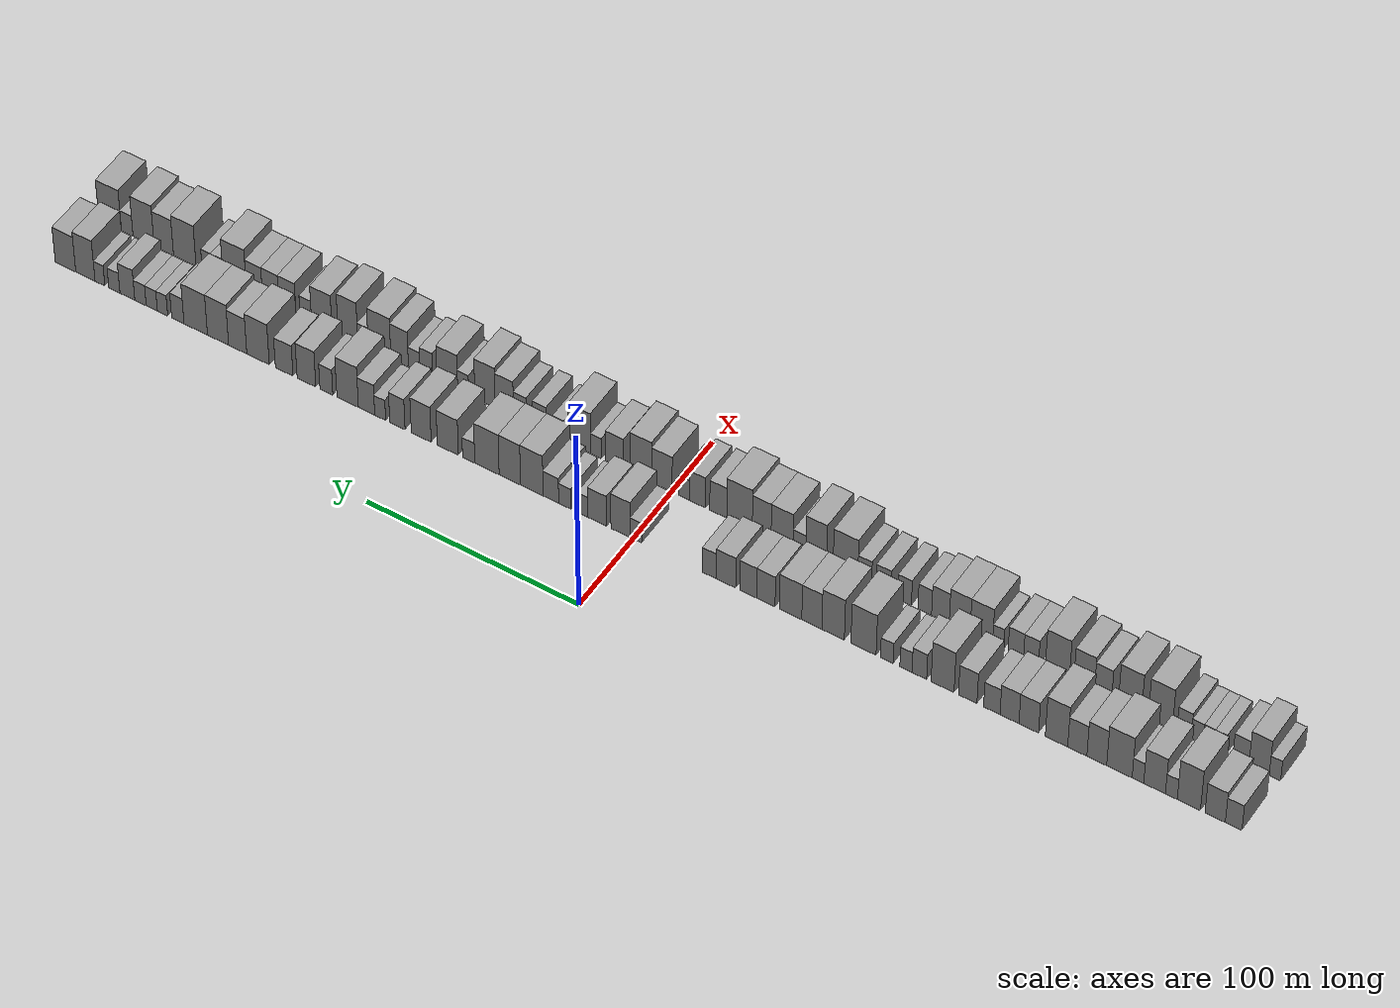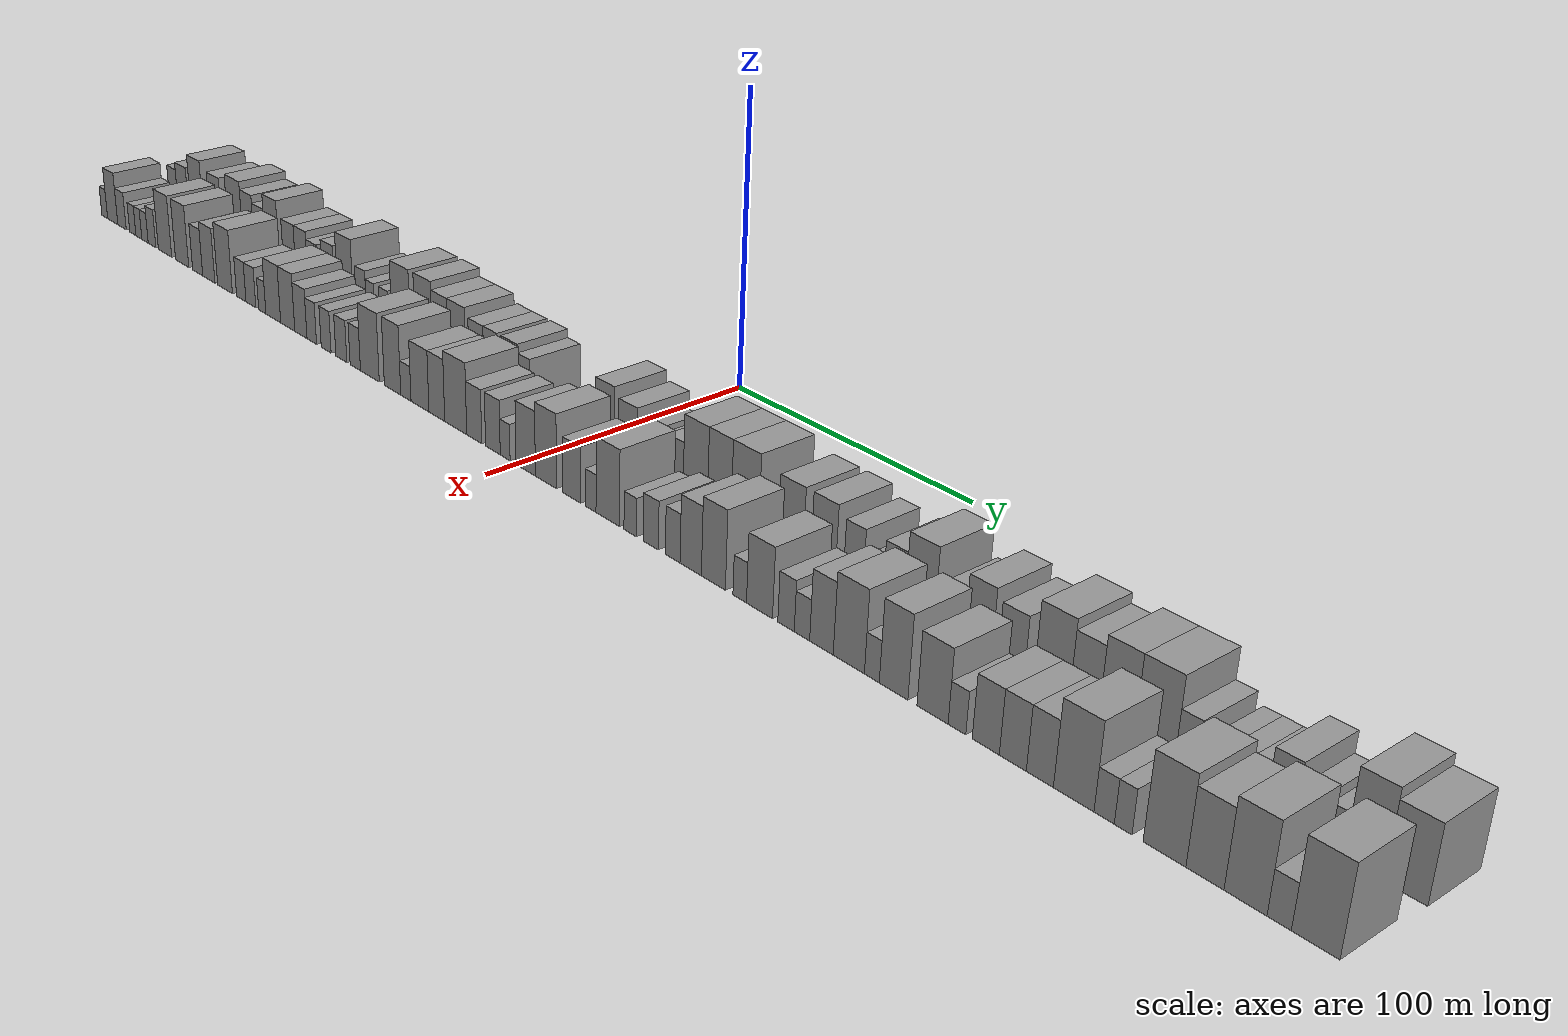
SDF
<sdf version="1.6">
 <world name="default">
  <scene>
   <sky><clouds><speed>12</speed></clouds></sky>
   <ambient>0.4 0.4 0.4 1</ambient>
   <background>0.7 0.7 0.7 1</background>
   <shadows>1</shadows>
  </scene>
  <gravity>0 0 -9.8066</gravity>
  <magnetic_field>6e-06 2.3e-05 -4.2e-05</magnetic_field>
  <physics default="0" name="default_physics" type="ode">
   <ode>
    <solver>
     <type>quick</type>
     <iters>10</iters>
     <sor>1.0</sor>
     <use_dynamic_moi_rescaling>0</use_dynamic_moi_rescaling>
    </solver>
    <constraints>
     <cfm>0</cfm>
     <erp>0.2</erp>
     <contact_max_correcting_vel>100</contact_max_correcting_vel>
     <contact_surface_layer>0.001</contact_surface_layer>
    </constraints>
   </ode>
   <max_step_size>0.004</max_step_size>
   <real_time_factor>1</real_time_factor>
   <real_time_update_rate>250</real_time_update_rate>
  </physics>
  <light name="sun" type="directional">
   <pose>0 0 10 0 0 0</pose>
   <diffuse>0.8 0.8 0.8 1</diffuse>
   <specular>0.2 0.2 0.2 1</specular>
   <attenuation>
    <range>1000</range>
    <constant>0.9</constant>
    <linear>0.01</linear>
    <quadratic>0.001</quadratic>
   </attenuation>
   <direction>-0.5 0.1 -0.9</direction>
  </light>
  <model name="building_1">
   <static>1</static>
   <pose>50.0000 -271.3934 0 0.000000 0.000000 0.000000</pose>
   <link name="link">
    <pose>0 0 7.50 0 0 0</pose>
    <collision name="collision"><geometry><box><size>20.0000 7.2133 15.0000</size></box></geometry></collision>
    <visual name="visual">
     <cast_shadows>0</cast_shadows>
     <geometry><box><size>20.0000 7.2133 15.0000</size></box></geometry>
     <material>
      <script>
       <uri>model://grey_wall/materials/scripts</uri>
       <uri>model://grey_wall/materials/textures</uri>
       <name>vrc/grey_wall</name>
      </script>
     </material>
    </visual>
   </link>
  </model>
  <model name="building_2">
   <static>1</static>
   <pose>50.0000 -263.3516 0 0.000000 0.000000 0.000000</pose>
   <link name="link">
    <pose>0 0 9.00 0 0 0</pose>
    <collision name="collision"><geometry><box><size>20.0000 8.8703 18.0000</size></box></geometry></collision>
    <visual name="visual">
     <cast_shadows>0</cast_shadows>
     <geometry><box><size>20.0000 8.8703 18.0000</size></box></geometry>
     <material>
      <script>
       <uri>model://grey_wall/materials/scripts</uri>
       <uri>model://grey_wall/materials/textures</uri>
       <name>vrc/grey_wall</name>
      </script>
     </material>
    </visual>
   </link>
  </model>
  <model name="building_3">
   <static>1</static>
   <pose>50.0000 -251.8428 0 0.000000 0.000000 0.000000</pose>
   <link name="link">
    <pose>0 0 12.00 0 0 0</pose>
    <collision name="collision"><geometry><box><size>20.0000 10.1471 24.0000</size></box></geometry></collision>
    <visual name="visual">
     <cast_shadows>0</cast_shadows>
     <geometry><box><size>20.0000 10.1471 24.0000</size></box></geometry>
     <material>
      <script>
       <uri>model://grey_wall/materials/scripts</uri>
       <uri>model://grey_wall/materials/textures</uri>
       <name>vrc/grey_wall</name>
      </script>
     </material>
    </visual>
   </link>
  </model>
  <model name="building_4">
   <static>1</static>
   <pose>50.0000 -244.1770 0 0.000000 0.000000 0.000000</pose>
   <link name="link">
    <pose>0 0 6.00 0 0 0</pose>
    <collision name="collision"><geometry><box><size>20.0000 5.1846 12.0000</size></box></geometry></collision>
    <visual name="visual">
     <cast_shadows>0</cast_shadows>
     <geometry><box><size>20.0000 5.1846 12.0000</size></box></geometry>
     <material>
      <script>
       <uri>model://grey_wall/materials/scripts</uri>
       <uri>model://grey_wall/materials/textures</uri>
       <name>vrc/grey_wall</name>
      </script>
     </material>
    </visual>
   </link>
  </model>
  <model name="building_5">
   <static>1</static>
   <pose>50.0000 -236.8170 0 0.000000 0.000000 0.000000</pose>
   <link name="link">
    <pose>0 0 10.50 0 0 0</pose>
    <collision name="collision"><geometry><box><size>20.0000 9.5352 21.0000</size></box></geometry></collision>
    <visual name="visual">
     <cast_shadows>0</cast_shadows>
     <geometry><box><size>20.0000 9.5352 21.0000</size></box></geometry>
     <material>
      <script>
       <uri>model://grey_wall/materials/scripts</uri>
       <uri>model://grey_wall/materials/textures</uri>
       <name>vrc/grey_wall</name>
      </script>
     </material>
    </visual>
   </link>
  </model>
  <model name="building_6">
   <static>1</static>
   <pose>50.0000 -229.4893 0 0.000000 0.000000 0.000000</pose>
   <link name="link">
    <pose>0 0 6.00 0 0 0</pose>
    <collision name="collision"><geometry><box><size>20.0000 5.1203 12.0000</size></box></geometry></collision>
    <visual name="visual">
     <cast_shadows>0</cast_shadows>
     <geometry><box><size>20.0000 5.1203 12.0000</size></box></geometry>
     <material>
      <script>
       <uri>model://grey_wall/materials/scripts</uri>
       <uri>model://grey_wall/materials/textures</uri>
       <name>vrc/grey_wall</name>
      </script>
     </material>
    </visual>
   </link>
  </model>
  <model name="building_7">
   <static>1</static>
   <pose>50.0000 -221.3045 0 0.000000 0.000000 0.000000</pose>
   <link name="link">
    <pose>0 0 12.00 0 0 0</pose>
    <collision name="collision"><geometry><box><size>20.0000 11.2494 24.0000</size></box></geometry></collision>
    <visual name="visual">
     <cast_shadows>0</cast_shadows>
     <geometry><box><size>20.0000 11.2494 24.0000</size></box></geometry>
     <material>
      <script>
       <uri>model://grey_wall/materials/scripts</uri>
       <uri>model://grey_wall/materials/textures</uri>
       <name>vrc/grey_wall</name>
      </script>
     </material>
    </visual>
   </link>
  </model>
  <model name="building_8">
   <static>1</static>
   <pose>50.0000 -211.3098 0 0.000000 0.000000 0.000000</pose>
   <link name="link">
    <pose>0 0 10.50 0 0 0</pose>
    <collision name="collision"><geometry><box><size>20.0000 8.7400 21.0000</size></box></geometry></collision>
    <visual name="visual">
     <cast_shadows>0</cast_shadows>
     <geometry><box><size>20.0000 8.7400 21.0000</size></box></geometry>
     <material>
      <script>
       <uri>model://grey_wall/materials/scripts</uri>
       <uri>model://grey_wall/materials/textures</uri>
       <name>vrc/grey_wall</name>
      </script>
     </material>
    </visual>
   </link>
  </model>
  <model name="building_9">
   <static>1</static>
   <pose>50.0000 -202.6717 0 0.000000 0.000000 0.000000</pose>
   <link name="link">
    <pose>0 0 9.00 0 0 0</pose>
    <collision name="collision"><geometry><box><size>20.0000 8.5363 18.0000</size></box></geometry></collision>
    <visual name="visual">
     <cast_shadows>0</cast_shadows>
     <geometry><box><size>20.0000 8.5363 18.0000</size></box></geometry>
     <material>
      <script>
       <uri>model://grey_wall/materials/scripts</uri>
       <uri>model://grey_wall/materials/textures</uri>
       <name>vrc/grey_wall</name>
      </script>
     </material>
    </visual>
   </link>
  </model>
  <model name="building_10">
   <static>1</static>
   <pose>50.0000 -193.4217 0 0.000000 0.000000 0.000000</pose>
   <link name="link">
    <pose>0 0 12.00 0 0 0</pose>
    <collision name="collision"><geometry><box><size>20.0000 9.9637 24.0000</size></box></geometry></collision>
    <visual name="visual">
     <cast_shadows>0</cast_shadows>
     <geometry><box><size>20.0000 9.9637 24.0000</size></box></geometry>
     <material>
      <script>
       <uri>model://grey_wall/materials/scripts</uri>
       <uri>model://grey_wall/materials/textures</uri>
       <name>vrc/grey_wall</name>
      </script>
     </material>
    </visual>
   </link>
  </model>
  <model name="building_11">
   <static>1</static>
   <pose>50.0000 -181.0662 0 0.000000 0.000000 0.000000</pose>
   <link name="link">
    <pose>0 0 9.00 0 0 0</pose>
    <collision name="collision"><geometry><box><size>20.0000 8.7472 18.0000</size></box></geometry></collision>
    <visual name="visual">
     <cast_shadows>0</cast_shadows>
     <geometry><box><size>20.0000 8.7472 18.0000</size></box></geometry>
     <material>
      <script>
       <uri>model://grey_wall/materials/scripts</uri>
       <uri>model://grey_wall/materials/textures</uri>
       <name>vrc/grey_wall</name>
      </script>
     </material>
    </visual>
   </link>
  </model>
  <model name="building_12">
   <static>1</static>
   <pose>50.0000 -172.4583 0 0.000000 0.000000 0.000000</pose>
   <link name="link">
    <pose>0 0 9.00 0 0 0</pose>
    <collision name="collision"><geometry><box><size>20.0000 8.4685 18.0000</size></box></geometry></collision>
    <visual name="visual">
     <cast_shadows>0</cast_shadows>
     <geometry><box><size>20.0000 8.4685 18.0000</size></box></geometry>
     <material>
      <script>
       <uri>model://grey_wall/materials/scripts</uri>
       <uri>model://grey_wall/materials/textures</uri>
       <name>vrc/grey_wall</name>
      </script>
     </material>
    </visual>
   </link>
  </model>
  <model name="building_13">
   <static>1</static>
   <pose>50.0000 -164.5516 0 0.000000 0.000000 0.000000</pose>
   <link name="link">
    <pose>0 0 7.50 0 0 0</pose>
    <collision name="collision"><geometry><box><size>20.0000 7.3451 15.0000</size></box></geometry></collision>
    <visual name="visual">
     <cast_shadows>0</cast_shadows>
     <geometry><box><size>20.0000 7.3451 15.0000</size></box></geometry>
     <material>
      <script>
       <uri>model://grey_wall/materials/scripts</uri>
       <uri>model://grey_wall/materials/textures</uri>
       <name>vrc/grey_wall</name>
      </script>
     </material>
    </visual>
   </link>
  </model>
  <model name="building_14">
   <static>1</static>
   <pose>50.0000 -153.7193 0 0.000000 0.000000 0.000000</pose>
   <link name="link">
    <pose>0 0 9.00 0 0 0</pose>
    <collision name="collision"><geometry><box><size>20.0000 8.3196 18.0000</size></box></geometry></collision>
    <visual name="visual">
     <cast_shadows>0</cast_shadows>
     <geometry><box><size>20.0000 8.3196 18.0000</size></box></geometry>
     <material>
      <script>
       <uri>model://grey_wall/materials/scripts</uri>
       <uri>model://grey_wall/materials/textures</uri>
       <name>vrc/grey_wall</name>
      </script>
     </material>
    </visual>
   </link>
  </model>
  <model name="building_15">
   <static>1</static>
   <pose>50.0000 -142.3722 0 0.000000 0.000000 0.000000</pose>
   <link name="link">
    <pose>0 0 12.00 0 0 0</pose>
    <collision name="collision"><geometry><box><size>20.0000 10.3744 24.0000</size></box></geometry></collision>
    <visual name="visual">
     <cast_shadows>0</cast_shadows>
     <geometry><box><size>20.0000 10.3744 24.0000</size></box></geometry>
     <material>
      <script>
       <uri>model://grey_wall/materials/scripts</uri>
       <uri>model://grey_wall/materials/textures</uri>
       <name>vrc/grey_wall</name>
      </script>
     </material>
    </visual>
   </link>
  </model>
  <model name="building_16">
   <static>1</static>
   <pose>50.0000 -131.8775 0 0.000000 0.000000 0.000000</pose>
   <link name="link">
    <pose>0 0 7.50 0 0 0</pose>
    <collision name="collision"><geometry><box><size>20.0000 6.6150 15.0000</size></box></geometry></collision>
    <visual name="visual">
     <cast_shadows>0</cast_shadows>
     <geometry><box><size>20.0000 6.6150 15.0000</size></box></geometry>
     <material>
      <script>
       <uri>model://grey_wall/materials/scripts</uri>
       <uri>model://grey_wall/materials/textures</uri>
       <name>vrc/grey_wall</name>
      </script>
     </material>
    </visual>
   </link>
  </model>
  <model name="building_17">
   <static>1</static>
   <pose>50.0000 -125.8137 0 0.000000 0.000000 0.000000</pose>
   <link name="link">
    <pose>0 0 6.00 0 0 0</pose>
    <collision name="collision"><geometry><box><size>20.0000 5.5126 12.0000</size></box></geometry></collision>
    <visual name="visual">
     <cast_shadows>0</cast_shadows>
     <geometry><box><size>20.0000 5.5126 12.0000</size></box></geometry>
     <material>
      <script>
       <uri>model://grey_wall/materials/scripts</uri>
       <uri>model://grey_wall/materials/textures</uri>
       <name>vrc/grey_wall</name>
      </script>
     </material>
    </visual>
   </link>
  </model>
  <model name="building_18">
   <static>1</static>
   <pose>50.0000 -117.1598 0 0.000000 0.000000 0.000000</pose>
   <link name="link">
    <pose>0 0 6.00 0 0 0</pose>
    <collision name="collision"><geometry><box><size>20.0000 5.7952 12.0000</size></box></geometry></collision>
    <visual name="visual">
     <cast_shadows>0</cast_shadows>
     <geometry><box><size>20.0000 5.7952 12.0000</size></box></geometry>
     <material>
      <script>
       <uri>model://grey_wall/materials/scripts</uri>
       <uri>model://grey_wall/materials/textures</uri>
       <name>vrc/grey_wall</name>
      </script>
     </material>
    </visual>
   </link>
  </model>
  <model name="building_19">
   <static>1</static>
   <pose>50.0000 -106.5253 0 0.000000 0.000000 0.000000</pose>
   <link name="link">
    <pose>0 0 12.00 0 0 0</pose>
    <collision name="collision"><geometry><box><size>20.0000 11.4739 24.0000</size></box></geometry></collision>
    <visual name="visual">
     <cast_shadows>0</cast_shadows>
     <geometry><box><size>20.0000 11.4739 24.0000</size></box></geometry>
     <material>
      <script>
       <uri>model://grey_wall/materials/scripts</uri>
       <uri>model://grey_wall/materials/textures</uri>
       <name>vrc/grey_wall</name>
      </script>
     </material>
    </visual>
   </link>
  </model>
  <model name="building_20">
   <static>1</static>
   <pose>50.0000 -92.6263 0 0.000000 0.000000 0.000000</pose>
   <link name="link">
    <pose>0 0 12.00 0 0 0</pose>
    <collision name="collision"><geometry><box><size>20.0000 10.3240 24.0000</size></box></geometry></collision>
    <visual name="visual">
     <cast_shadows>0</cast_shadows>
     <geometry><box><size>20.0000 10.3240 24.0000</size></box></geometry>
     <material>
      <script>
       <uri>model://grey_wall/materials/scripts</uri>
       <uri>model://grey_wall/materials/textures</uri>
       <name>vrc/grey_wall</name>
      </script>
     </material>
    </visual>
   </link>
  </model>
  <model name="building_21">
   <static>1</static>
   <pose>50.0000 -82.8727 0 0.000000 0.000000 0.000000</pose>
   <link name="link">
    <pose>0 0 10.50 0 0 0</pose>
    <collision name="collision"><geometry><box><size>20.0000 9.1832 21.0000</size></box></geometry></collision>
    <visual name="visual">
     <cast_shadows>0</cast_shadows>
     <geometry><box><size>20.0000 9.1832 21.0000</size></box></geometry>
     <material>
      <script>
       <uri>model://grey_wall/materials/scripts</uri>
       <uri>model://grey_wall/materials/textures</uri>
       <name>vrc/grey_wall</name>
      </script>
     </material>
    </visual>
   </link>
  </model>
  <model name="building_22">
   <static>1</static>
   <pose>50.0000 -73.1384 0 0.000000 0.000000 0.000000</pose>
   <link name="link">
    <pose>0 0 10.50 0 0 0</pose>
    <collision name="collision"><geometry><box><size>20.0000 10.2854 21.0000</size></box></geometry></collision>
    <visual name="visual">
     <cast_shadows>0</cast_shadows>
     <geometry><box><size>20.0000 10.2854 21.0000</size></box></geometry>
     <material>
      <script>
       <uri>model://grey_wall/materials/scripts</uri>
       <uri>model://grey_wall/materials/textures</uri>
       <name>vrc/grey_wall</name>
      </script>
     </material>
    </visual>
   </link>
  </model>
  <model name="building_23">
   <static>1</static>
   <pose>50.0000 -61.7829 0 0.000000 0.000000 0.000000</pose>
   <link name="link">
    <pose>0 0 9.00 0 0 0</pose>
    <collision name="collision"><geometry><box><size>20.0000 8.4257 18.0000</size></box></geometry></collision>
    <visual name="visual">
     <cast_shadows>0</cast_shadows>
     <geometry><box><size>20.0000 8.4257 18.0000</size></box></geometry>
     <material>
      <script>
       <uri>model://grey_wall/materials/scripts</uri>
       <uri>model://grey_wall/materials/textures</uri>
       <name>vrc/grey_wall</name>
      </script>
     </material>
    </visual>
   </link>
  </model>
  <model name="building_24">
   <static>1</static>
   <pose>50.0000 -53.6768 0 0.000000 0.000000 0.000000</pose>
   <link name="link">
    <pose>0 0 9.00 0 0 0</pose>
    <collision name="collision"><geometry><box><size>20.0000 7.7865 18.0000</size></box></geometry></collision>
    <visual name="visual">
     <cast_shadows>0</cast_shadows>
     <geometry><box><size>20.0000 7.7865 18.0000</size></box></geometry>
     <material>
      <script>
       <uri>model://grey_wall/materials/scripts</uri>
       <uri>model://grey_wall/materials/textures</uri>
       <name>vrc/grey_wall</name>
      </script>
     </material>
    </visual>
   </link>
  </model>
  <model name="building_25">
   <static>1</static>
   <pose>50.0000 -43.2927 0 0.000000 0.000000 0.000000</pose>
   <link name="link">
    <pose>0 0 9.00 0 0 0</pose>
    <collision name="collision"><geometry><box><size>20.0000 8.9817 18.0000</size></box></geometry></collision>
    <visual name="visual">
     <cast_shadows>0</cast_shadows>
     <geometry><box><size>20.0000 8.9817 18.0000</size></box></geometry>
     <material>
      <script>
       <uri>model://grey_wall/materials/scripts</uri>
       <uri>model://grey_wall/materials/textures</uri>
       <name>vrc/grey_wall</name>
      </script>
     </material>
    </visual>
   </link>
  </model>
  <model name="building_26">
   <static>1</static>
   <pose>50.0000 -35.5720 0 0.000000 0.000000 0.000000</pose>
   <link name="link">
    <pose>0 0 7.50 0 0 0</pose>
    <collision name="collision"><geometry><box><size>20.0000 6.4597 15.0000</size></box></geometry></collision>
    <visual name="visual">
     <cast_shadows>0</cast_shadows>
     <geometry><box><size>20.0000 6.4597 15.0000</size></box></geometry>
     <material>
      <script>
       <uri>model://grey_wall/materials/scripts</uri>
       <uri>model://grey_wall/materials/textures</uri>
       <name>vrc/grey_wall</name>
      </script>
     </material>
    </visual>
   </link>
  </model>
  <model name="building_27">
   <static>1</static>
   <pose>50.0000 -1.3399 0 0.000000 0.000000 0.000000</pose>
   <link name="link">
    <pose>0 0 6.00 0 0 0</pose>
    <collision name="collision"><geometry><box><size>20.0000 5.3348 12.0000</size></box></geometry></collision>
    <visual name="visual">
     <cast_shadows>0</cast_shadows>
     <geometry><box><size>20.0000 5.3348 12.0000</size></box></geometry>
     <material>
      <script>
       <uri>model://grey_wall/materials/scripts</uri>
       <uri>model://grey_wall/materials/textures</uri>
       <name>vrc/grey_wall</name>
      </script>
     </material>
    </visual>
   </link>
  </model>
  <model name="building_28">
   <static>1</static>
   <pose>50.0000 5.8778 0 0.000000 0.000000 0.000000</pose>
   <link name="link">
    <pose>0 0 10.50 0 0 0</pose>
    <collision name="collision"><geometry><box><size>20.0000 9.1007 21.0000</size></box></geometry></collision>
    <visual name="visual">
     <cast_shadows>0</cast_shadows>
     <geometry><box><size>20.0000 9.1007 21.0000</size></box></geometry>
     <material>
      <script>
       <uri>model://grey_wall/materials/scripts</uri>
       <uri>model://grey_wall/materials/textures</uri>
       <name>vrc/grey_wall</name>
      </script>
     </material>
    </visual>
   </link>
  </model>
  <model name="building_29">
   <static>1</static>
   <pose>50.0000 16.8329 0 0.000000 0.000000 0.000000</pose>
   <link name="link">
    <pose>0 0 9.00 0 0 0</pose>
    <collision name="collision"><geometry><box><size>20.0000 8.8094 18.0000</size></box></geometry></collision>
    <visual name="visual">
     <cast_shadows>0</cast_shadows>
     <geometry><box><size>20.0000 8.8094 18.0000</size></box></geometry>
     <material>
      <script>
       <uri>model://grey_wall/materials/scripts</uri>
       <uri>model://grey_wall/materials/textures</uri>
       <name>vrc/grey_wall</name>
      </script>
     </material>
    </visual>
   </link>
  </model>
  <model name="building_30">
   <static>1</static>
   <pose>50.0000 23.7386 0 0.000000 0.000000 0.000000</pose>
   <link name="link">
    <pose>0 0 6.00 0 0 0</pose>
    <collision name="collision"><geometry><box><size>20.0000 5.0021 12.0000</size></box></geometry></collision>
    <visual name="visual">
     <cast_shadows>0</cast_shadows>
     <geometry><box><size>20.0000 5.0021 12.0000</size></box></geometry>
     <material>
      <script>
       <uri>model://grey_wall/materials/scripts</uri>
       <uri>model://grey_wall/materials/textures</uri>
       <name>vrc/grey_wall</name>
      </script>
     </material>
    </visual>
   </link>
  </model>
  <model name="building_31">
   <static>1</static>
   <pose>50.0000 32.1665 0 0.000000 0.000000 0.000000</pose>
   <link name="link">
    <pose>0 0 6.00 0 0 0</pose>
    <collision name="collision"><geometry><box><size>20.0000 5.8538 12.0000</size></box></geometry></collision>
    <visual name="visual">
     <cast_shadows>0</cast_shadows>
     <geometry><box><size>20.0000 5.8538 12.0000</size></box></geometry>
     <material>
      <script>
       <uri>model://grey_wall/materials/scripts</uri>
       <uri>model://grey_wall/materials/textures</uri>
       <name>vrc/grey_wall</name>
      </script>
     </material>
    </visual>
   </link>
  </model>
  <model name="building_32">
   <static>1</static>
   <pose>50.0000 38.7642 0 0.000000 0.000000 0.000000</pose>
   <link name="link">
    <pose>0 0 7.50 0 0 0</pose>
    <collision name="collision"><geometry><box><size>20.0000 7.3415 15.0000</size></box></geometry></collision>
    <visual name="visual">
     <cast_shadows>0</cast_shadows>
     <geometry><box><size>20.0000 7.3415 15.0000</size></box></geometry>
     <material>
      <script>
       <uri>model://grey_wall/materials/scripts</uri>
       <uri>model://grey_wall/materials/textures</uri>
       <name>vrc/grey_wall</name>
      </script>
     </material>
    </visual>
   </link>
  </model>
  <model name="building_33">
   <static>1</static>
   <pose>50.0000 47.8110 0 0.000000 0.000000 0.000000</pose>
   <link name="link">
    <pose>0 0 12.00 0 0 0</pose>
    <collision name="collision"><geometry><box><size>20.0000 10.7521 24.0000</size></box></geometry></collision>
    <visual name="visual">
     <cast_shadows>0</cast_shadows>
     <geometry><box><size>20.0000 10.7521 24.0000</size></box></geometry>
     <material>
      <script>
       <uri>model://grey_wall/materials/scripts</uri>
       <uri>model://grey_wall/materials/textures</uri>
       <name>vrc/grey_wall</name>
      </script>
     </material>
    </visual>
   </link>
  </model>
  <model name="building_34">
   <static>1</static>
   <pose>50.0000 58.2903 0 0.000000 0.000000 0.000000</pose>
   <link name="link">
    <pose>0 0 12.00 0 0 0</pose>
    <collision name="collision"><geometry><box><size>20.0000 10.2065 24.0000</size></box></geometry></collision>
    <visual name="visual">
     <cast_shadows>0</cast_shadows>
     <geometry><box><size>20.0000 10.2065 24.0000</size></box></geometry>
     <material>
      <script>
       <uri>model://grey_wall/materials/scripts</uri>
       <uri>model://grey_wall/materials/textures</uri>
       <name>vrc/grey_wall</name>
      </script>
     </material>
    </visual>
   </link>
  </model>
  <model name="building_35">
   <static>1</static>
   <pose>50.0000 69.1989 0 0.000000 0.000000 0.000000</pose>
   <link name="link">
    <pose>0 0 12.00 0 0 0</pose>
    <collision name="collision"><geometry><box><size>20.0000 11.6106 24.0000</size></box></geometry></collision>
    <visual name="visual">
     <cast_shadows>0</cast_shadows>
     <geometry><box><size>20.0000 11.6106 24.0000</size></box></geometry>
     <material>
      <script>
       <uri>model://grey_wall/materials/scripts</uri>
       <uri>model://grey_wall/materials/textures</uri>
       <name>vrc/grey_wall</name>
      </script>
     </material>
    </visual>
   </link>
  </model>
  <model name="building_36">
   <static>1</static>
   <pose>50.0000 77.9321 0 0.000000 0.000000 0.000000</pose>
   <link name="link">
    <pose>0 0 6.00 0 0 0</pose>
    <collision name="collision"><geometry><box><size>20.0000 5.8558 12.0000</size></box></geometry></collision>
    <visual name="visual">
     <cast_shadows>0</cast_shadows>
     <geometry><box><size>20.0000 5.8558 12.0000</size></box></geometry>
     <material>
      <script>
       <uri>model://grey_wall/materials/scripts</uri>
       <uri>model://grey_wall/materials/textures</uri>
       <name>vrc/grey_wall</name>
      </script>
     </material>
    </visual>
   </link>
  </model>
  <model name="building_37">
   <static>1</static>
   <pose>50.0000 87.9176 0 0.000000 0.000000 0.000000</pose>
   <link name="link">
    <pose>0 0 10.50 0 0 0</pose>
    <collision name="collision"><geometry><box><size>20.0000 10.1152 21.0000</size></box></geometry></collision>
    <visual name="visual">
     <cast_shadows>0</cast_shadows>
     <geometry><box><size>20.0000 10.1152 21.0000</size></box></geometry>
     <material>
      <script>
       <uri>model://grey_wall/materials/scripts</uri>
       <uri>model://grey_wall/materials/textures</uri>
       <name>vrc/grey_wall</name>
      </script>
     </material>
    </visual>
   </link>
  </model>
  <model name="building_38">
   <static>1</static>
   <pose>50.0000 100.7672 0 0.000000 0.000000 0.000000</pose>
   <link name="link">
    <pose>0 0 10.50 0 0 0</pose>
    <collision name="collision"><geometry><box><size>20.0000 9.5838 21.0000</size></box></geometry></collision>
    <visual name="visual">
     <cast_shadows>0</cast_shadows>
     <geometry><box><size>20.0000 9.5838 21.0000</size></box></geometry>
     <material>
      <script>
       <uri>model://grey_wall/materials/scripts</uri>
       <uri>model://grey_wall/materials/textures</uri>
       <name>vrc/grey_wall</name>
      </script>
     </material>
    </visual>
   </link>
  </model>
  <model name="building_39">
   <static>1</static>
   <pose>50.0000 112.2447 0 0.000000 0.000000 0.000000</pose>
   <link name="link">
    <pose>0 0 9.00 0 0 0</pose>
    <collision name="collision"><geometry><box><size>20.0000 7.3713 18.0000</size></box></geometry></collision>
    <visual name="visual">
     <cast_shadows>0</cast_shadows>
     <geometry><box><size>20.0000 7.3713 18.0000</size></box></geometry>
     <material>
      <script>
       <uri>model://grey_wall/materials/scripts</uri>
       <uri>model://grey_wall/materials/textures</uri>
       <name>vrc/grey_wall</name>
      </script>
     </material>
    </visual>
   </link>
  </model>
  <model name="building_40">
   <static>1</static>
   <pose>50.0000 120.5763 0 0.000000 0.000000 0.000000</pose>
   <link name="link">
    <pose>0 0 6.00 0 0 0</pose>
    <collision name="collision"><geometry><box><size>20.0000 5.2918 12.0000</size></box></geometry></collision>
    <visual name="visual">
     <cast_shadows>0</cast_shadows>
     <geometry><box><size>20.0000 5.2918 12.0000</size></box></geometry>
     <material>
      <script>
       <uri>model://grey_wall/materials/scripts</uri>
       <uri>model://grey_wall/materials/textures</uri>
       <name>vrc/grey_wall</name>
      </script>
     </material>
    </visual>
   </link>
  </model>
  <model name="building_41">
   <static>1</static>
   <pose>50.0000 127.1940 0 0.000000 0.000000 0.000000</pose>
   <link name="link">
    <pose>0 0 9.00 0 0 0</pose>
    <collision name="collision"><geometry><box><size>20.0000 7.9437 18.0000</size></box></geometry></collision>
    <visual name="visual">
     <cast_shadows>0</cast_shadows>
     <geometry><box><size>20.0000 7.9437 18.0000</size></box></geometry>
     <material>
      <script>
       <uri>model://grey_wall/materials/scripts</uri>
       <uri>model://grey_wall/materials/textures</uri>
       <name>vrc/grey_wall</name>
      </script>
     </material>
    </visual>
   </link>
  </model>
  <model name="building_42">
   <static>1</static>
   <pose>50.0000 136.3898 0 0.000000 0.000000 0.000000</pose>
   <link name="link">
    <pose>0 0 12.00 0 0 0</pose>
    <collision name="collision"><geometry><box><size>20.0000 10.4479 24.0000</size></box></geometry></collision>
    <visual name="visual">
     <cast_shadows>0</cast_shadows>
     <geometry><box><size>20.0000 10.4479 24.0000</size></box></geometry>
     <material>
      <script>
       <uri>model://grey_wall/materials/scripts</uri>
       <uri>model://grey_wall/materials/textures</uri>
       <name>vrc/grey_wall</name>
      </script>
     </material>
    </visual>
   </link>
  </model>
  <model name="building_43">
   <static>1</static>
   <pose>50.0000 146.7610 0 0.000000 0.000000 0.000000</pose>
   <link name="link">
    <pose>0 0 7.50 0 0 0</pose>
    <collision name="collision"><geometry><box><size>20.0000 6.2945 15.0000</size></box></geometry></collision>
    <visual name="visual">
     <cast_shadows>0</cast_shadows>
     <geometry><box><size>20.0000 6.2945 15.0000</size></box></geometry>
     <material>
      <script>
       <uri>model://grey_wall/materials/scripts</uri>
       <uri>model://grey_wall/materials/textures</uri>
       <name>vrc/grey_wall</name>
      </script>
     </material>
    </visual>
   </link>
  </model>
  <model name="building_44">
   <static>1</static>
   <pose>50.0000 156.4740 0 0.000000 0.000000 0.000000</pose>
   <link name="link">
    <pose>0 0 10.50 0 0 0</pose>
    <collision name="collision"><geometry><box><size>20.0000 9.1314 21.0000</size></box></geometry></collision>
    <visual name="visual">
     <cast_shadows>0</cast_shadows>
     <geometry><box><size>20.0000 9.1314 21.0000</size></box></geometry>
     <material>
      <script>
       <uri>model://grey_wall/materials/scripts</uri>
       <uri>model://grey_wall/materials/textures</uri>
       <name>vrc/grey_wall</name>
      </script>
     </material>
    </visual>
   </link>
  </model>
  <model name="building_45">
   <static>1</static>
   <pose>50.0000 167.3634 0 0.000000 0.000000 0.000000</pose>
   <link name="link">
    <pose>0 0 9.00 0 0 0</pose>
    <collision name="collision"><geometry><box><size>20.0000 8.6474 18.0000</size></box></geometry></collision>
    <visual name="visual">
     <cast_shadows>0</cast_shadows>
     <geometry><box><size>20.0000 8.6474 18.0000</size></box></geometry>
     <material>
      <script>
       <uri>model://grey_wall/materials/scripts</uri>
       <uri>model://grey_wall/materials/textures</uri>
       <name>vrc/grey_wall</name>
      </script>
     </material>
    </visual>
   </link>
  </model>
  <model name="building_46">
   <static>1</static>
   <pose>50.0000 180.2306 0 0.000000 0.000000 0.000000</pose>
   <link name="link">
    <pose>0 0 12.00 0 0 0</pose>
    <collision name="collision"><geometry><box><size>20.0000 11.0870 24.0000</size></box></geometry></collision>
    <visual name="visual">
     <cast_shadows>0</cast_shadows>
     <geometry><box><size>20.0000 11.0870 24.0000</size></box></geometry>
     <material>
      <script>
       <uri>model://grey_wall/materials/scripts</uri>
       <uri>model://grey_wall/materials/textures</uri>
       <name>vrc/grey_wall</name>
      </script>
     </material>
    </visual>
   </link>
  </model>
  <model name="building_47">
   <static>1</static>
   <pose>50.0000 190.2564 0 0.000000 0.000000 0.000000</pose>
   <link name="link">
    <pose>0 0 10.50 0 0 0</pose>
    <collision name="collision"><geometry><box><size>20.0000 8.9645 21.0000</size></box></geometry></collision>
    <visual name="visual">
     <cast_shadows>0</cast_shadows>
     <geometry><box><size>20.0000 8.9645 21.0000</size></box></geometry>
     <material>
      <script>
       <uri>model://grey_wall/materials/scripts</uri>
       <uri>model://grey_wall/materials/textures</uri>
       <name>vrc/grey_wall</name>
      </script>
     </material>
    </visual>
   </link>
  </model>
  <model name="building_48">
   <static>1</static>
   <pose>50.0000 199.9749 0 0.000000 0.000000 0.000000</pose>
   <link name="link">
    <pose>0 0 12.00 0 0 0</pose>
    <collision name="collision"><geometry><box><size>20.0000 10.4727 24.0000</size></box></geometry></collision>
    <visual name="visual">
     <cast_shadows>0</cast_shadows>
     <geometry><box><size>20.0000 10.4727 24.0000</size></box></geometry>
     <material>
      <script>
       <uri>model://grey_wall/materials/scripts</uri>
       <uri>model://grey_wall/materials/textures</uri>
       <name>vrc/grey_wall</name>
      </script>
     </material>
    </visual>
   </link>
  </model>
  <model name="building_49">
   <static>1</static>
   <pose>50.0000 211.0418 0 0.000000 0.000000 0.000000</pose>
   <link name="link">
    <pose>0 0 12.00 0 0 0</pose>
    <collision name="collision"><geometry><box><size>20.0000 11.6610 24.0000</size></box></geometry></collision>
    <visual name="visual">
     <cast_shadows>0</cast_shadows>
     <geometry><box><size>20.0000 11.6610 24.0000</size></box></geometry>
     <material>
      <script>
       <uri>model://grey_wall/materials/scripts</uri>
       <uri>model://grey_wall/materials/textures</uri>
       <name>vrc/grey_wall</name>
      </script>
     </material>
    </visual>
   </link>
  </model>
  <model name="building_50">
   <static>1</static>
   <pose>50.0000 219.9304 0 0.000000 0.000000 0.000000</pose>
   <link name="link">
    <pose>0 0 7.50 0 0 0</pose>
    <collision name="collision"><geometry><box><size>20.0000 6.1162 15.0000</size></box></geometry></collision>
    <visual name="visual">
     <cast_shadows>0</cast_shadows>
     <geometry><box><size>20.0000 6.1162 15.0000</size></box></geometry>
     <material>
      <script>
       <uri>model://grey_wall/materials/scripts</uri>
       <uri>model://grey_wall/materials/textures</uri>
       <name>vrc/grey_wall</name>
      </script>
     </material>
    </visual>
   </link>
  </model>
  <model name="building_51">
   <static>1</static>
   <pose>50.0000 227.5612 0 0.000000 0.000000 0.000000</pose>
   <link name="link">
    <pose>0 0 6.00 0 0 0</pose>
    <collision name="collision"><geometry><box><size>20.0000 5.1453 12.0000</size></box></geometry></collision>
    <visual name="visual">
     <cast_shadows>0</cast_shadows>
     <geometry><box><size>20.0000 5.1453 12.0000</size></box></geometry>
     <material>
      <script>
       <uri>model://grey_wall/materials/scripts</uri>
       <uri>model://grey_wall/materials/textures</uri>
       <name>vrc/grey_wall</name>
      </script>
     </material>
    </visual>
   </link>
  </model>
  <model name="building_52">
   <static>1</static>
   <pose>50.0000 232.9234 0 0.000000 0.000000 0.000000</pose>
   <link name="link">
    <pose>0 0 6.00 0 0 0</pose>
    <collision name="collision"><geometry><box><size>20.0000 5.5791 12.0000</size></box></geometry></collision>
    <visual name="visual">
     <cast_shadows>0</cast_shadows>
     <geometry><box><size>20.0000 5.5791 12.0000</size></box></geometry>
     <material>
      <script>
       <uri>model://grey_wall/materials/scripts</uri>
       <uri>model://grey_wall/materials/textures</uri>
       <name>vrc/grey_wall</name>
      </script>
     </material>
    </visual>
   </link>
  </model>
  <model name="building_53">
   <static>1</static>
   <pose>50.0000 238.5586 0 0.000000 0.000000 0.000000</pose>
   <link name="link">
    <pose>0 0 6.00 0 0 0</pose>
    <collision name="collision"><geometry><box><size>20.0000 5.6915 12.0000</size></box></geometry></collision>
    <visual name="visual">
     <cast_shadows>0</cast_shadows>
     <geometry><box><size>20.0000 5.6915 12.0000</size></box></geometry>
     <material>
      <script>
       <uri>model://grey_wall/materials/scripts</uri>
       <uri>model://grey_wall/materials/textures</uri>
       <name>vrc/grey_wall</name>
      </script>
     </material>
    </visual>
   </link>
  </model>
  <model name="building_54">
   <static>1</static>
   <pose>50.0000 245.1342 0 0.000000 0.000000 0.000000</pose>
   <link name="link">
    <pose>0 0 9.00 0 0 0</pose>
    <collision name="collision"><geometry><box><size>20.0000 7.4597 18.0000</size></box></geometry></collision>
    <visual name="visual">
     <cast_shadows>0</cast_shadows>
     <geometry><box><size>20.0000 7.4597 18.0000</size></box></geometry>
     <material>
      <script>
       <uri>model://grey_wall/materials/scripts</uri>
       <uri>model://grey_wall/materials/textures</uri>
       <name>vrc/grey_wall</name>
      </script>
     </material>
    </visual>
   </link>
  </model>
  <model name="building_55">
   <static>1</static>
   <pose>50.0000 251.6517 0 0.000000 0.000000 0.000000</pose>
   <link name="link">
    <pose>0 0 6.00 0 0 0</pose>
    <collision name="collision"><geometry><box><size>20.0000 5.5754 12.0000</size></box></geometry></collision>
    <visual name="visual">
     <cast_shadows>0</cast_shadows>
     <geometry><box><size>20.0000 5.5754 12.0000</size></box></geometry>
     <material>
      <script>
       <uri>model://grey_wall/materials/scripts</uri>
       <uri>model://grey_wall/materials/textures</uri>
       <name>vrc/grey_wall</name>
      </script>
     </material>
    </visual>
   </link>
  </model>
  <model name="building_56">
   <static>1</static>
   <pose>50.0000 258.8911 0 0.000000 0.000000 0.000000</pose>
   <link name="link">
    <pose>0 0 6.00 0 0 0</pose>
    <collision name="collision"><geometry><box><size>20.0000 4.9034 12.0000</size></box></geometry></collision>
    <visual name="visual">
     <cast_shadows>0</cast_shadows>
     <geometry><box><size>20.0000 4.9034 12.0000</size></box></geometry>
     <material>
      <script>
       <uri>model://grey_wall/materials/scripts</uri>
       <uri>model://grey_wall/materials/textures</uri>
       <name>vrc/grey_wall</name>
      </script>
     </material>
    </visual>
   </link>
  </model>
  <model name="building_57">
   <static>1</static>
   <pose>50.0000 266.1980 0 0.000000 0.000000 0.000000</pose>
   <link name="link">
    <pose>0 0 12.00 0 0 0</pose>
    <collision name="collision"><geometry><box><size>20.0000 9.7103 24.0000</size></box></geometry></collision>
    <visual name="visual">
     <cast_shadows>0</cast_shadows>
     <geometry><box><size>20.0000 9.7103 24.0000</size></box></geometry>
     <material>
      <script>
       <uri>model://grey_wall/materials/scripts</uri>
       <uri>model://grey_wall/materials/textures</uri>
       <name>vrc/grey_wall</name>
      </script>
     </material>
    </visual>
   </link>
  </model>
  <model name="building_58">
   <static>1</static>
   <pose>50.0000 276.2072 0 0.000000 0.000000 0.000000</pose>
   <link name="link">
    <pose>0 0 10.50 0 0 0</pose>
    <collision name="collision"><geometry><box><size>20.0000 10.3082 21.0000</size></box></geometry></collision>
    <visual name="visual">
     <cast_shadows>0</cast_shadows>
     <geometry><box><size>20.0000 10.3082 21.0000</size></box></geometry>
     <material>
      <script>
       <uri>model://grey_wall/materials/scripts</uri>
       <uri>model://grey_wall/materials/textures</uri>
       <name>vrc/grey_wall</name>
      </script>
     </material>
    </visual>
   </link>
  </model>
  <model name="building_59">
   <static>1</static>
   <pose>79.0000 -273.4948 0 0.000000 0.000000 0.000000</pose>
   <link name="link">
    <pose>0 0 6.00 0 0 0</pose>
    <collision name="collision"><geometry><box><size>20.0000 5.0103 12.0000</size></box></geometry></collision>
    <visual name="visual">
     <cast_shadows>0</cast_shadows>
     <geometry><box><size>20.0000 5.0103 12.0000</size></box></geometry>
     <material>
      <script>
       <uri>model://grey_wall/materials/scripts</uri>
       <uri>model://grey_wall/materials/textures</uri>
       <name>vrc/grey_wall</name>
      </script>
     </material>
    </visual>
   </link>
  </model>
  <model name="building_60">
   <static>1</static>
   <pose>79.0000 -266.5489 0 0.000000 0.000000 0.000000</pose>
   <link name="link">
    <pose>0 0 10.50 0 0 0</pose>
    <collision name="collision"><geometry><box><size>20.0000 8.8815 21.0000</size></box></geometry></collision>
    <visual name="visual">
     <cast_shadows>0</cast_shadows>
     <geometry><box><size>20.0000 8.8815 21.0000</size></box></geometry>
     <material>
      <script>
       <uri>model://grey_wall/materials/scripts</uri>
       <uri>model://grey_wall/materials/textures</uri>
       <name>vrc/grey_wall</name>
      </script>
     </material>
    </visual>
   </link>
  </model>
  <model name="building_61">
   <static>1</static>
   <pose>79.0000 -258.5615 0 0.000000 0.000000 0.000000</pose>
   <link name="link">
    <pose>0 0 7.50 0 0 0</pose>
    <collision name="collision"><geometry><box><size>20.0000 7.0934 15.0000</size></box></geometry></collision>
    <visual name="visual">
     <cast_shadows>0</cast_shadows>
     <geometry><box><size>20.0000 7.0934 15.0000</size></box></geometry>
     <material>
      <script>
       <uri>model://grey_wall/materials/scripts</uri>
       <uri>model://grey_wall/materials/textures</uri>
       <name>vrc/grey_wall</name>
      </script>
     </material>
    </visual>
   </link>
  </model>
  <model name="building_62">
   <static>1</static>
   <pose>79.0000 -249.4196 0 0.000000 0.000000 0.000000</pose>
   <link name="link">
    <pose>0 0 6.00 0 0 0</pose>
    <collision name="collision"><geometry><box><size>20.0000 5.1904 12.0000</size></box></geometry></collision>
    <visual name="visual">
     <cast_shadows>0</cast_shadows>
     <geometry><box><size>20.0000 5.1904 12.0000</size></box></geometry>
     <material>
      <script>
       <uri>model://grey_wall/materials/scripts</uri>
       <uri>model://grey_wall/materials/textures</uri>
       <name>vrc/grey_wall</name>
      </script>
     </material>
    </visual>
   </link>
  </model>
  <model name="building_63">
   <static>1</static>
   <pose>79.0000 -244.3865 0 0.000000 0.000000 0.000000</pose>
   <link name="link">
    <pose>0 0 6.00 0 0 0</pose>
    <collision name="collision"><geometry><box><size>20.0000 4.8758 12.0000</size></box></geometry></collision>
    <visual name="visual">
     <cast_shadows>0</cast_shadows>
     <geometry><box><size>20.0000 4.8758 12.0000</size></box></geometry>
     <material>
      <script>
       <uri>model://grey_wall/materials/scripts</uri>
       <uri>model://grey_wall/materials/textures</uri>
       <name>vrc/grey_wall</name>
      </script>
     </material>
    </visual>
   </link>
  </model>
  <model name="building_64">
   <static>1</static>
   <pose>79.0000 -239.3299 0 0.000000 0.000000 0.000000</pose>
   <link name="link">
    <pose>0 0 6.00 0 0 0</pose>
    <collision name="collision"><geometry><box><size>20.0000 5.2375 12.0000</size></box></geometry></collision>
    <visual name="visual">
     <cast_shadows>0</cast_shadows>
     <geometry><box><size>20.0000 5.2375 12.0000</size></box></geometry>
     <material>
      <script>
       <uri>model://grey_wall/materials/scripts</uri>
       <uri>model://grey_wall/materials/textures</uri>
       <name>vrc/grey_wall</name>
      </script>
     </material>
    </visual>
   </link>
  </model>
  <model name="building_65">
   <static>1</static>
   <pose>79.0000 -233.5546 0 0.000000 0.000000 0.000000</pose>
   <link name="link">
    <pose>0 0 7.50 0 0 0</pose>
    <collision name="collision"><geometry><box><size>20.0000 6.3130 15.0000</size></box></geometry></collision>
    <visual name="visual">
     <cast_shadows>0</cast_shadows>
     <geometry><box><size>20.0000 6.3130 15.0000</size></box></geometry>
     <material>
      <script>
       <uri>model://grey_wall/materials/scripts</uri>
       <uri>model://grey_wall/materials/textures</uri>
       <name>vrc/grey_wall</name>
      </script>
     </material>
    </visual>
   </link>
  </model>
  <model name="building_66">
   <static>1</static>
   <pose>79.0000 -223.0500 0 0.000000 0.000000 0.000000</pose>
   <link name="link">
    <pose>0 0 12.00 0 0 0</pose>
    <collision name="collision"><geometry><box><size>20.0000 10.6962 24.0000</size></box></geometry></collision>
    <visual name="visual">
     <cast_shadows>0</cast_shadows>
     <geometry><box><size>20.0000 10.6962 24.0000</size></box></geometry>
     <material>
      <script>
       <uri>model://grey_wall/materials/scripts</uri>
       <uri>model://grey_wall/materials/textures</uri>
       <name>vrc/grey_wall</name>
      </script>
     </material>
    </visual>
   </link>
  </model>
  <model name="building_67">
   <static>1</static>
   <pose>79.0000 -209.5441 0 0.000000 0.000000 0.000000</pose>
   <link name="link">
    <pose>0 0 12.00 0 0 0</pose>
    <collision name="collision"><geometry><box><size>20.0000 10.3157 24.0000</size></box></geometry></collision>
    <visual name="visual">
     <cast_shadows>0</cast_shadows>
     <geometry><box><size>20.0000 10.3157 24.0000</size></box></geometry>
     <material>
      <script>
       <uri>model://grey_wall/materials/scripts</uri>
       <uri>model://grey_wall/materials/textures</uri>
       <name>vrc/grey_wall</name>
      </script>
     </material>
    </visual>
   </link>
  </model>
  <model name="building_68">
   <static>1</static>
   <pose>79.0000 -197.5531 0 0.000000 0.000000 0.000000</pose>
   <link name="link">
    <pose>0 0 9.00 0 0 0</pose>
    <collision name="collision"><geometry><box><size>20.0000 7.6663 18.0000</size></box></geometry></collision>
    <visual name="visual">
     <cast_shadows>0</cast_shadows>
     <geometry><box><size>20.0000 7.6663 18.0000</size></box></geometry>
     <material>
      <script>
       <uri>model://grey_wall/materials/scripts</uri>
       <uri>model://grey_wall/materials/textures</uri>
       <name>vrc/grey_wall</name>
      </script>
     </material>
    </visual>
   </link>
  </model>
  <model name="building_69">
   <static>1</static>
   <pose>79.0000 -189.1175 0 0.000000 0.000000 0.000000</pose>
   <link name="link">
    <pose>0 0 10.50 0 0 0</pose>
    <collision name="collision"><geometry><box><size>20.0000 9.2048 21.0000</size></box></geometry></collision>
    <visual name="visual">
     <cast_shadows>0</cast_shadows>
     <geometry><box><size>20.0000 9.2048 21.0000</size></box></geometry>
     <material>
      <script>
       <uri>model://grey_wall/materials/scripts</uri>
       <uri>model://grey_wall/materials/textures</uri>
       <name>vrc/grey_wall</name>
      </script>
     </material>
    </visual>
   </link>
  </model>
  <model name="building_70">
   <static>1</static>
   <pose>79.0000 -177.1046 0 0.000000 0.000000 0.000000</pose>
   <link name="link">
    <pose>0 0 12.00 0 0 0</pose>
    <collision name="collision"><geometry><box><size>20.0000 10.8210 24.0000</size></box></geometry></collision>
    <visual name="visual">
     <cast_shadows>0</cast_shadows>
     <geometry><box><size>20.0000 10.8210 24.0000</size></box></geometry>
     <material>
      <script>
       <uri>model://grey_wall/materials/scripts</uri>
       <uri>model://grey_wall/materials/textures</uri>
       <name>vrc/grey_wall</name>
      </script>
     </material>
    </visual>
   </link>
  </model>
  <model name="building_71">
   <static>1</static>
   <pose>79.0000 -165.3211 0 0.000000 0.000000 0.000000</pose>
   <link name="link">
    <pose>0 0 7.50 0 0 0</pose>
    <collision name="collision"><geometry><box><size>20.0000 6.7460 15.0000</size></box></geometry></collision>
    <visual name="visual">
     <cast_shadows>0</cast_shadows>
     <geometry><box><size>20.0000 6.7460 15.0000</size></box></geometry>
     <material>
      <script>
       <uri>model://grey_wall/materials/scripts</uri>
       <uri>model://grey_wall/materials/textures</uri>
       <name>vrc/grey_wall</name>
      </script>
     </material>
    </visual>
   </link>
  </model>
  <model name="building_72">
   <static>1</static>
   <pose>79.0000 -158.4674 0 0.000000 0.000000 0.000000</pose>
   <link name="link">
    <pose>0 0 7.50 0 0 0</pose>
    <collision name="collision"><geometry><box><size>20.0000 6.9614 15.0000</size></box></geometry></collision>
    <visual name="visual">
     <cast_shadows>0</cast_shadows>
     <geometry><box><size>20.0000 6.9614 15.0000</size></box></geometry>
     <material>
      <script>
       <uri>model://grey_wall/materials/scripts</uri>
       <uri>model://grey_wall/materials/textures</uri>
       <name>vrc/grey_wall</name>
      </script>
     </material>
    </visual>
   </link>
  </model>
  <model name="building_73">
   <static>1</static>
   <pose>79.0000 -150.4704 0 0.000000 0.000000 0.000000</pose>
   <link name="link">
    <pose>0 0 6.00 0 0 0</pose>
    <collision name="collision"><geometry><box><size>20.0000 5.0326 12.0000</size></box></geometry></collision>
    <visual name="visual">
     <cast_shadows>0</cast_shadows>
     <geometry><box><size>20.0000 5.0326 12.0000</size></box></geometry>
     <material>
      <script>
       <uri>model://grey_wall/materials/scripts</uri>
       <uri>model://grey_wall/materials/textures</uri>
       <name>vrc/grey_wall</name>
      </script>
     </material>
    </visual>
   </link>
  </model>
  <model name="building_74">
   <static>1</static>
   <pose>79.0000 -142.8758 0 0.000000 0.000000 0.000000</pose>
   <link name="link">
    <pose>0 0 10.50 0 0 0</pose>
    <collision name="collision"><geometry><box><size>20.0000 10.1565 21.0000</size></box></geometry></collision>
    <visual name="visual">
     <cast_shadows>0</cast_shadows>
     <geometry><box><size>20.0000 10.1565 21.0000</size></box></geometry>
     <material>
      <script>
       <uri>model://grey_wall/materials/scripts</uri>
       <uri>model://grey_wall/materials/textures</uri>
       <name>vrc/grey_wall</name>
      </script>
     </material>
    </visual>
   </link>
  </model>
  <model name="building_75">
   <static>1</static>
   <pose>79.0000 -133.0584 0 0.000000 0.000000 0.000000</pose>
   <link name="link">
    <pose>0 0 10.50 0 0 0</pose>
    <collision name="collision"><geometry><box><size>20.0000 9.4782 21.0000</size></box></geometry></collision>
    <visual name="visual">
     <cast_shadows>0</cast_shadows>
     <geometry><box><size>20.0000 9.4782 21.0000</size></box></geometry>
     <material>
      <script>
       <uri>model://grey_wall/materials/scripts</uri>
       <uri>model://grey_wall/materials/textures</uri>
       <name>vrc/grey_wall</name>
      </script>
     </material>
    </visual>
   </link>
  </model>
  <model name="building_76">
   <static>1</static>
   <pose>79.0000 -124.2952 0 0.000000 0.000000 0.000000</pose>
   <link name="link">
    <pose>0 0 9.00 0 0 0</pose>
    <collision name="collision"><geometry><box><size>20.0000 8.0482 18.0000</size></box></geometry></collision>
    <visual name="visual">
     <cast_shadows>0</cast_shadows>
     <geometry><box><size>20.0000 8.0482 18.0000</size></box></geometry>
     <material>
      <script>
       <uri>model://grey_wall/materials/scripts</uri>
       <uri>model://grey_wall/materials/textures</uri>
       <name>vrc/grey_wall</name>
      </script>
     </material>
    </visual>
   </link>
  </model>
  <model name="building_77">
   <static>1</static>
   <pose>79.0000 -117.1596 0 0.000000 0.000000 0.000000</pose>
   <link name="link">
    <pose>0 0 7.50 0 0 0</pose>
    <collision name="collision"><geometry><box><size>20.0000 6.2230 15.0000</size></box></geometry></collision>
    <visual name="visual">
     <cast_shadows>0</cast_shadows>
     <geometry><box><size>20.0000 6.2230 15.0000</size></box></geometry>
     <material>
      <script>
       <uri>model://grey_wall/materials/scripts</uri>
       <uri>model://grey_wall/materials/textures</uri>
       <name>vrc/grey_wall</name>
      </script>
     </material>
    </visual>
   </link>
  </model>
  <model name="building_78">
   <static>1</static>
   <pose>79.0000 -107.8837 0 0.000000 0.000000 0.000000</pose>
   <link name="link">
    <pose>0 0 7.50 0 0 0</pose>
    <collision name="collision"><geometry><box><size>20.0000 6.3289 15.0000</size></box></geometry></collision>
    <visual name="visual">
     <cast_shadows>0</cast_shadows>
     <geometry><box><size>20.0000 6.3289 15.0000</size></box></geometry>
     <material>
      <script>
       <uri>model://grey_wall/materials/scripts</uri>
       <uri>model://grey_wall/materials/textures</uri>
       <name>vrc/grey_wall</name>
      </script>
     </material>
    </visual>
   </link>
  </model>
  <model name="building_79">
   <static>1</static>
   <pose>79.0000 -98.2653 0 0.000000 0.000000 0.000000</pose>
   <link name="link">
    <pose>0 0 7.50 0 0 0</pose>
    <collision name="collision"><geometry><box><size>20.0000 6.9080 15.0000</size></box></geometry></collision>
    <visual name="visual">
     <cast_shadows>0</cast_shadows>
     <geometry><box><size>20.0000 6.9080 15.0000</size></box></geometry>
     <material>
      <script>
       <uri>model://grey_wall/materials/scripts</uri>
       <uri>model://grey_wall/materials/textures</uri>
       <name>vrc/grey_wall</name>
      </script>
     </material>
    </visual>
   </link>
  </model>
  <model name="building_80">
   <static>1</static>
   <pose>79.0000 -89.6210 0 0.000000 0.000000 0.000000</pose>
   <link name="link">
    <pose>0 0 7.50 0 0 0</pose>
    <collision name="collision"><geometry><box><size>20.0000 6.3806 15.0000</size></box></geometry></collision>
    <visual name="visual">
     <cast_shadows>0</cast_shadows>
     <geometry><box><size>20.0000 6.3806 15.0000</size></box></geometry>
     <material>
      <script>
       <uri>model://grey_wall/materials/scripts</uri>
       <uri>model://grey_wall/materials/textures</uri>
       <name>vrc/grey_wall</name>
      </script>
     </material>
    </visual>
   </link>
  </model>
  <model name="building_81">
   <static>1</static>
   <pose>79.0000 -80.7626 0 0.000000 0.000000 0.000000</pose>
   <link name="link">
    <pose>0 0 12.00 0 0 0</pose>
    <collision name="collision"><geometry><box><size>20.0000 11.3363 24.0000</size></box></geometry></collision>
    <visual name="visual">
     <cast_shadows>0</cast_shadows>
     <geometry><box><size>20.0000 11.3363 24.0000</size></box></geometry>
     <material>
      <script>
       <uri>model://grey_wall/materials/scripts</uri>
       <uri>model://grey_wall/materials/textures</uri>
       <name>vrc/grey_wall</name>
      </script>
     </material>
    </visual>
   </link>
  </model>
  <model name="building_82">
   <static>1</static>
   <pose>79.0000 -67.2696 0 0.000000 0.000000 0.000000</pose>
   <link name="link">
    <pose>0 0 12.00 0 0 0</pose>
    <collision name="collision"><geometry><box><size>20.0000 9.6497 24.0000</size></box></geometry></collision>
    <visual name="visual">
     <cast_shadows>0</cast_shadows>
     <geometry><box><size>20.0000 9.6497 24.0000</size></box></geometry>
     <material>
      <script>
       <uri>model://grey_wall/materials/scripts</uri>
       <uri>model://grey_wall/materials/textures</uri>
       <name>vrc/grey_wall</name>
      </script>
     </material>
    </visual>
   </link>
  </model>
  <model name="building_83">
   <static>1</static>
   <pose>79.0000 -59.4937 0 0.000000 0.000000 0.000000</pose>
   <link name="link">
    <pose>0 0 6.00 0 0 0</pose>
    <collision name="collision"><geometry><box><size>20.0000 5.9021 12.0000</size></box></geometry></collision>
    <visual name="visual">
     <cast_shadows>0</cast_shadows>
     <geometry><box><size>20.0000 5.9021 12.0000</size></box></geometry>
     <material>
      <script>
       <uri>model://grey_wall/materials/scripts</uri>
       <uri>model://grey_wall/materials/textures</uri>
       <name>vrc/grey_wall</name>
      </script>
     </material>
    </visual>
   </link>
  </model>
  <model name="building_84">
   <static>1</static>
   <pose>79.0000 -51.4613 0 0.000000 0.000000 0.000000</pose>
   <link name="link">
    <pose>0 0 10.50 0 0 0</pose>
    <collision name="collision"><geometry><box><size>20.0000 10.1627 21.0000</size></box></geometry></collision>
    <visual name="visual">
     <cast_shadows>0</cast_shadows>
     <geometry><box><size>20.0000 10.1627 21.0000</size></box></geometry>
     <material>
      <script>
       <uri>model://grey_wall/materials/scripts</uri>
       <uri>model://grey_wall/materials/textures</uri>
       <name>vrc/grey_wall</name>
      </script>
     </material>
    </visual>
   </link>
  </model>
  <model name="building_85">
   <static>1</static>
   <pose>79.0000 -42.0060 0 0.000000 0.000000 0.000000</pose>
   <link name="link">
    <pose>0 0 10.50 0 0 0</pose>
    <collision name="collision"><geometry><box><size>20.0000 8.7480 21.0000</size></box></geometry></collision>
    <visual name="visual">
     <cast_shadows>0</cast_shadows>
     <geometry><box><size>20.0000 8.7480 21.0000</size></box></geometry>
     <material>
      <script>
       <uri>model://grey_wall/materials/scripts</uri>
       <uri>model://grey_wall/materials/textures</uri>
       <name>vrc/grey_wall</name>
      </script>
     </material>
    </visual>
   </link>
  </model>
  <model name="building_86">
   <static>1</static>
   <pose>79.0000 -31.6701 0 0.000000 0.000000 0.000000</pose>
   <link name="link">
    <pose>0 0 12.00 0 0 0</pose>
    <collision name="collision"><geometry><box><size>20.0000 11.9237 24.0000</size></box></geometry></collision>
    <visual name="visual">
     <cast_shadows>0</cast_shadows>
     <geometry><box><size>20.0000 11.9237 24.0000</size></box></geometry>
     <material>
      <script>
       <uri>model://grey_wall/materials/scripts</uri>
       <uri>model://grey_wall/materials/textures</uri>
       <name>vrc/grey_wall</name>
      </script>
     </material>
    </visual>
   </link>
  </model>
  <model name="building_87">
   <static>1</static>
   <pose>79.0000 -21.7378 0 0.000000 0.000000 0.000000</pose>
   <link name="link">
    <pose>0 0 9.00 0 0 0</pose>
    <collision name="collision"><geometry><box><size>20.0000 7.9410 18.0000</size></box></geometry></collision>
    <visual name="visual">
     <cast_shadows>0</cast_shadows>
     <geometry><box><size>20.0000 7.9410 18.0000</size></box></geometry>
     <material>
      <script>
       <uri>model://grey_wall/materials/scripts</uri>
       <uri>model://grey_wall/materials/textures</uri>
       <name>vrc/grey_wall</name>
      </script>
     </material>
    </visual>
   </link>
  </model>
  <model name="building_88">
   <static>1</static>
   <pose>79.0000 -11.9650 0 0.000000 0.000000 0.000000</pose>
   <link name="link">
    <pose>0 0 9.00 0 0 0</pose>
    <collision name="collision"><geometry><box><size>20.0000 7.6044 18.0000</size></box></geometry></collision>
    <visual name="visual">
     <cast_shadows>0</cast_shadows>
     <geometry><box><size>20.0000 7.6044 18.0000</size></box></geometry>
     <material>
      <script>
       <uri>model://grey_wall/materials/scripts</uri>
       <uri>model://grey_wall/materials/textures</uri>
       <name>vrc/grey_wall</name>
      </script>
     </material>
    </visual>
   </link>
  </model>
  <model name="building_89">
   <static>1</static>
   <pose>79.0000 -5.6486 0 0.000000 0.000000 0.000000</pose>
   <link name="link">
    <pose>0 0 6.00 0 0 0</pose>
    <collision name="collision"><geometry><box><size>20.0000 5.0285 12.0000</size></box></geometry></collision>
    <visual name="visual">
     <cast_shadows>0</cast_shadows>
     <geometry><box><size>20.0000 5.0285 12.0000</size></box></geometry>
     <material>
      <script>
       <uri>model://grey_wall/materials/scripts</uri>
       <uri>model://grey_wall/materials/textures</uri>
       <name>vrc/grey_wall</name>
      </script>
     </material>
    </visual>
   </link>
  </model>
  <model name="building_90">
   <static>1</static>
   <pose>79.0000 4.6921 0 0.000000 0.000000 0.000000</pose>
   <link name="link">
    <pose>0 0 10.50 0 0 0</pose>
    <collision name="collision"><geometry><box><size>20.0000 9.6528 21.0000</size></box></geometry></collision>
    <visual name="visual">
     <cast_shadows>0</cast_shadows>
     <geometry><box><size>20.0000 9.6528 21.0000</size></box></geometry>
     <material>
      <script>
       <uri>model://grey_wall/materials/scripts</uri>
       <uri>model://grey_wall/materials/textures</uri>
       <name>vrc/grey_wall</name>
      </script>
     </material>
    </visual>
   </link>
  </model>
  <model name="building_91">
   <static>1</static>
   <pose>79.0000 14.6517 0 0.000000 0.000000 0.000000</pose>
   <link name="link">
    <pose>0 0 12.00 0 0 0</pose>
    <collision name="collision"><geometry><box><size>20.0000 10.2664 24.0000</size></box></geometry></collision>
    <visual name="visual">
     <cast_shadows>0</cast_shadows>
     <geometry><box><size>20.0000 10.2664 24.0000</size></box></geometry>
     <material>
      <script>
       <uri>model://grey_wall/materials/scripts</uri>
       <uri>model://grey_wall/materials/textures</uri>
       <name>vrc/grey_wall</name>
      </script>
     </material>
    </visual>
   </link>
  </model>
  <model name="building_92">
   <static>1</static>
   <pose>79.0000 27.0608 0 0.000000 0.000000 0.000000</pose>
   <link name="link">
    <pose>0 0 9.00 0 0 0</pose>
    <collision name="collision"><geometry><box><size>20.0000 8.5518 18.0000</size></box></geometry></collision>
    <visual name="visual">
     <cast_shadows>0</cast_shadows>
     <geometry><box><size>20.0000 8.5518 18.0000</size></box></geometry>
     <material>
      <script>
       <uri>model://grey_wall/materials/scripts</uri>
       <uri>model://grey_wall/materials/textures</uri>
       <name>vrc/grey_wall</name>
      </script>
     </material>
    </visual>
   </link>
  </model>
  <model name="building_93">
   <static>1</static>
   <pose>79.0000 35.8652 0 0.000000 0.000000 0.000000</pose>
   <link name="link">
    <pose>0 0 6.00 0 0 0</pose>
    <collision name="collision"><geometry><box><size>20.0000 5.0569 12.0000</size></box></geometry></collision>
    <visual name="visual">
     <cast_shadows>0</cast_shadows>
     <geometry><box><size>20.0000 5.0569 12.0000</size></box></geometry>
     <material>
      <script>
       <uri>model://grey_wall/materials/scripts</uri>
       <uri>model://grey_wall/materials/textures</uri>
       <name>vrc/grey_wall</name>
      </script>
     </material>
    </visual>
   </link>
  </model>
  <model name="building_94">
   <static>1</static>
   <pose>79.0000 43.7217 0 0.000000 0.000000 0.000000</pose>
   <link name="link">
    <pose>0 0 12.00 0 0 0</pose>
    <collision name="collision"><geometry><box><size>20.0000 10.6561 24.0000</size></box></geometry></collision>
    <visual name="visual">
     <cast_shadows>0</cast_shadows>
     <geometry><box><size>20.0000 10.6561 24.0000</size></box></geometry>
     <material>
      <script>
       <uri>model://grey_wall/materials/scripts</uri>
       <uri>model://grey_wall/materials/textures</uri>
       <name>vrc/grey_wall</name>
      </script>
     </material>
    </visual>
   </link>
  </model>
  <model name="building_95">
   <static>1</static>
   <pose>79.0000 53.8186 0 0.000000 0.000000 0.000000</pose>
   <link name="link">
    <pose>0 0 6.00 0 0 0</pose>
    <collision name="collision"><geometry><box><size>20.0000 5.5377 12.0000</size></box></geometry></collision>
    <visual name="visual">
     <cast_shadows>0</cast_shadows>
     <geometry><box><size>20.0000 5.5377 12.0000</size></box></geometry>
     <material>
      <script>
       <uri>model://grey_wall/materials/scripts</uri>
       <uri>model://grey_wall/materials/textures</uri>
       <name>vrc/grey_wall</name>
      </script>
     </material>
    </visual>
   </link>
  </model>
  <model name="building_96">
   <static>1</static>
   <pose>79.0000 62.8398 0 0.000000 0.000000 0.000000</pose>
   <link name="link">
    <pose>0 0 7.50 0 0 0</pose>
    <collision name="collision"><geometry><box><size>20.0000 6.5047 15.0000</size></box></geometry></collision>
    <visual name="visual">
     <cast_shadows>0</cast_shadows>
     <geometry><box><size>20.0000 6.5047 15.0000</size></box></geometry>
     <material>
      <script>
       <uri>model://grey_wall/materials/scripts</uri>
       <uri>model://grey_wall/materials/textures</uri>
       <name>vrc/grey_wall</name>
      </script>
     </material>
    </visual>
   </link>
  </model>
  <model name="building_97">
   <static>1</static>
   <pose>79.0000 72.1973 0 0.000000 0.000000 0.000000</pose>
   <link name="link">
    <pose>0 0 7.50 0 0 0</pose>
    <collision name="collision"><geometry><box><size>20.0000 6.2102 15.0000</size></box></geometry></collision>
    <visual name="visual">
     <cast_shadows>0</cast_shadows>
     <geometry><box><size>20.0000 6.2102 15.0000</size></box></geometry>
     <material>
      <script>
       <uri>model://grey_wall/materials/scripts</uri>
       <uri>model://grey_wall/materials/textures</uri>
       <name>vrc/grey_wall</name>
      </script>
     </material>
    </visual>
   </link>
  </model>
  <model name="building_98">
   <static>1</static>
   <pose>79.0000 79.7293 0 0.000000 0.000000 0.000000</pose>
   <link name="link">
    <pose>0 0 10.50 0 0 0</pose>
    <collision name="collision"><geometry><box><size>20.0000 8.8536 21.0000</size></box></geometry></collision>
    <visual name="visual">
     <cast_shadows>0</cast_shadows>
     <geometry><box><size>20.0000 8.8536 21.0000</size></box></geometry>
     <material>
      <script>
       <uri>model://grey_wall/materials/scripts</uri>
       <uri>model://grey_wall/materials/textures</uri>
       <name>vrc/grey_wall</name>
      </script>
     </material>
    </visual>
   </link>
  </model>
  <model name="building_99">
   <static>1</static>
   <pose>79.0000 89.0230 0 0.000000 0.000000 0.000000</pose>
   <link name="link">
    <pose>0 0 12.00 0 0 0</pose>
    <collision name="collision"><geometry><box><size>20.0000 9.7339 24.0000</size></box></geometry></collision>
    <visual name="visual">
     <cast_shadows>0</cast_shadows>
     <geometry><box><size>20.0000 9.7339 24.0000</size></box></geometry>
     <material>
      <script>
       <uri>model://grey_wall/materials/scripts</uri>
       <uri>model://grey_wall/materials/textures</uri>
       <name>vrc/grey_wall</name>
      </script>
     </material>
    </visual>
   </link>
  </model>
  <model name="building_100">
   <static>1</static>
   <pose>79.0000 99.5625 0 0.000000 0.000000 0.000000</pose>
   <link name="link">
    <pose>0 0 6.00 0 0 0</pose>
    <collision name="collision"><geometry><box><size>20.0000 5.3451 12.0000</size></box></geometry></collision>
    <visual name="visual">
     <cast_shadows>0</cast_shadows>
     <geometry><box><size>20.0000 5.3451 12.0000</size></box></geometry>
     <material>
      <script>
       <uri>model://grey_wall/materials/scripts</uri>
       <uri>model://grey_wall/materials/textures</uri>
       <name>vrc/grey_wall</name>
      </script>
     </material>
    </visual>
   </link>
  </model>
  <model name="building_101">
   <static>1</static>
   <pose>79.0000 107.2636 0 0.000000 0.000000 0.000000</pose>
   <link name="link">
    <pose>0 0 10.50 0 0 0</pose>
    <collision name="collision"><geometry><box><size>20.0000 10.0570 21.0000</size></box></geometry></collision>
    <visual name="visual">
     <cast_shadows>0</cast_shadows>
     <geometry><box><size>20.0000 10.0570 21.0000</size></box></geometry>
     <material>
      <script>
       <uri>model://grey_wall/materials/scripts</uri>
       <uri>model://grey_wall/materials/textures</uri>
       <name>vrc/grey_wall</name>
      </script>
     </material>
    </visual>
   </link>
  </model>
  <model name="building_102">
   <static>1</static>
   <pose>79.0000 117.3871 0 0.000000 0.000000 0.000000</pose>
   <link name="link">
    <pose>0 0 7.50 0 0 0</pose>
    <collision name="collision"><geometry><box><size>20.0000 6.1901 15.0000</size></box></geometry></collision>
    <visual name="visual">
     <cast_shadows>0</cast_shadows>
     <geometry><box><size>20.0000 6.1901 15.0000</size></box></geometry>
     <material>
      <script>
       <uri>model://grey_wall/materials/scripts</uri>
       <uri>model://grey_wall/materials/textures</uri>
       <name>vrc/grey_wall</name>
      </script>
     </material>
    </visual>
   </link>
  </model>
  <model name="building_103">
   <static>1</static>
   <pose>79.0000 123.3277 0 0.000000 0.000000 0.000000</pose>
   <link name="link">
    <pose>0 0 6.00 0 0 0</pose>
    <collision name="collision"><geometry><box><size>20.0000 5.6911 12.0000</size></box></geometry></collision>
    <visual name="visual">
     <cast_shadows>0</cast_shadows>
     <geometry><box><size>20.0000 5.6911 12.0000</size></box></geometry>
     <material>
      <script>
       <uri>model://grey_wall/materials/scripts</uri>
       <uri>model://grey_wall/materials/textures</uri>
       <name>vrc/grey_wall</name>
      </script>
     </material>
    </visual>
   </link>
  </model>
  <model name="building_104">
   <static>1</static>
   <pose>79.0000 130.4423 0 0.000000 0.000000 0.000000</pose>
   <link name="link">
    <pose>0 0 10.50 0 0 0</pose>
    <collision name="collision"><geometry><box><size>20.0000 8.5381 21.0000</size></box></geometry></collision>
    <visual name="visual">
     <cast_shadows>0</cast_shadows>
     <geometry><box><size>20.0000 8.5381 21.0000</size></box></geometry>
     <material>
      <script>
       <uri>model://grey_wall/materials/scripts</uri>
       <uri>model://grey_wall/materials/textures</uri>
       <name>vrc/grey_wall</name>
      </script>
     </material>
    </visual>
   </link>
  </model>
  <model name="building_105">
   <static>1</static>
   <pose>79.0000 140.2159 0 0.000000 0.000000 0.000000</pose>
   <link name="link">
    <pose>0 0 12.00 0 0 0</pose>
    <collision name="collision"><geometry><box><size>20.0000 11.0091 24.0000</size></box></geometry></collision>
    <visual name="visual">
     <cast_shadows>0</cast_shadows>
     <geometry><box><size>20.0000 11.0091 24.0000</size></box></geometry>
     <material>
      <script>
       <uri>model://grey_wall/materials/scripts</uri>
       <uri>model://grey_wall/materials/textures</uri>
       <name>vrc/grey_wall</name>
      </script>
     </material>
    </visual>
   </link>
  </model>
  <model name="building_106">
   <static>1</static>
   <pose>79.0000 148.2861 0 0.000000 0.000000 0.000000</pose>
   <link name="link">
    <pose>0 0 6.00 0 0 0</pose>
    <collision name="collision"><geometry><box><size>20.0000 5.1314 12.0000</size></box></geometry></collision>
    <visual name="visual">
     <cast_shadows>0</cast_shadows>
     <geometry><box><size>20.0000 5.1314 12.0000</size></box></geometry>
     <material>
      <script>
       <uri>model://grey_wall/materials/scripts</uri>
       <uri>model://grey_wall/materials/textures</uri>
       <name>vrc/grey_wall</name>
      </script>
     </material>
    </visual>
   </link>
  </model>
  <model name="building_107">
   <static>1</static>
   <pose>79.0000 155.6988 0 0.000000 0.000000 0.000000</pose>
   <link name="link">
    <pose>0 0 12.00 0 0 0</pose>
    <collision name="collision"><geometry><box><size>20.0000 9.6939 24.0000</size></box></geometry></collision>
    <visual name="visual">
     <cast_shadows>0</cast_shadows>
     <geometry><box><size>20.0000 9.6939 24.0000</size></box></geometry>
     <material>
      <script>
       <uri>model://grey_wall/materials/scripts</uri>
       <uri>model://grey_wall/materials/textures</uri>
       <name>vrc/grey_wall</name>
      </script>
     </material>
    </visual>
   </link>
  </model>
  <model name="building_108">
   <static>1</static>
   <pose>79.0000 168.6106 0 0.000000 0.000000 0.000000</pose>
   <link name="link">
    <pose>0 0 10.50 0 0 0</pose>
    <collision name="collision"><geometry><box><size>20.0000 10.1297 21.0000</size></box></geometry></collision>
    <visual name="visual">
     <cast_shadows>0</cast_shadows>
     <geometry><box><size>20.0000 10.1297 21.0000</size></box></geometry>
     <material>
      <script>
       <uri>model://grey_wall/materials/scripts</uri>
       <uri>model://grey_wall/materials/textures</uri>
       <name>vrc/grey_wall</name>
      </script>
     </material>
    </visual>
   </link>
  </model>
  <model name="building_109">
   <static>1</static>
   <pose>79.0000 176.4988 0 0.000000 0.000000 0.000000</pose>
   <link name="link">
    <pose>0 0 6.00 0 0 0</pose>
    <collision name="collision"><geometry><box><size>20.0000 5.6468 12.0000</size></box></geometry></collision>
    <visual name="visual">
     <cast_shadows>0</cast_shadows>
     <geometry><box><size>20.0000 5.6468 12.0000</size></box></geometry>
     <material>
      <script>
       <uri>model://grey_wall/materials/scripts</uri>
       <uri>model://grey_wall/materials/textures</uri>
       <name>vrc/grey_wall</name>
      </script>
     </material>
    </visual>
   </link>
  </model>
  <model name="building_110">
   <static>1</static>
   <pose>79.0000 185.5167 0 0.000000 0.000000 0.000000</pose>
   <link name="link">
    <pose>0 0 9.00 0 0 0</pose>
    <collision name="collision"><geometry><box><size>20.0000 8.3890 18.0000</size></box></geometry></collision>
    <visual name="visual">
     <cast_shadows>0</cast_shadows>
     <geometry><box><size>20.0000 8.3890 18.0000</size></box></geometry>
     <material>
      <script>
       <uri>model://grey_wall/materials/scripts</uri>
       <uri>model://grey_wall/materials/textures</uri>
       <name>vrc/grey_wall</name>
      </script>
     </material>
    </visual>
   </link>
  </model>
  <model name="building_111">
   <static>1</static>
   <pose>79.0000 193.7927 0 0.000000 0.000000 0.000000</pose>
   <link name="link">
    <pose>0 0 9.00 0 0 0</pose>
    <collision name="collision"><geometry><box><size>20.0000 8.1629 18.0000</size></box></geometry></collision>
    <visual name="visual">
     <cast_shadows>0</cast_shadows>
     <geometry><box><size>20.0000 8.1629 18.0000</size></box></geometry>
     <material>
      <script>
       <uri>model://grey_wall/materials/scripts</uri>
       <uri>model://grey_wall/materials/textures</uri>
       <name>vrc/grey_wall</name>
      </script>
     </material>
    </visual>
   </link>
  </model>
  <model name="building_112">
   <static>1</static>
   <pose>79.0000 201.8754 0 0.000000 0.000000 0.000000</pose>
   <link name="link">
    <pose>0 0 9.00 0 0 0</pose>
    <collision name="collision"><geometry><box><size>20.0000 8.0024 18.0000</size></box></geometry></collision>
    <visual name="visual">
     <cast_shadows>0</cast_shadows>
     <geometry><box><size>20.0000 8.0024 18.0000</size></box></geometry>
     <material>
      <script>
       <uri>model://grey_wall/materials/scripts</uri>
       <uri>model://grey_wall/materials/textures</uri>
       <name>vrc/grey_wall</name>
      </script>
     </material>
    </visual>
   </link>
  </model>
  <model name="building_113">
   <static>1</static>
   <pose>79.0000 211.6847 0 0.000000 0.000000 0.000000</pose>
   <link name="link">
    <pose>0 0 12.00 0 0 0</pose>
    <collision name="collision"><geometry><box><size>20.0000 11.6162 24.0000</size></box></geometry></collision>
    <visual name="visual">
     <cast_shadows>0</cast_shadows>
     <geometry><box><size>20.0000 11.6162 24.0000</size></box></geometry>
     <material>
      <script>
       <uri>model://grey_wall/materials/scripts</uri>
       <uri>model://grey_wall/materials/textures</uri>
       <name>vrc/grey_wall</name>
      </script>
     </material>
    </visual>
   </link>
  </model>
  <model name="building_114">
   <static>1</static>
   <pose>79.0000 220.3244 0 0.000000 0.000000 0.000000</pose>
   <link name="link">
    <pose>0 0 6.00 0 0 0</pose>
    <collision name="collision"><geometry><box><size>20.0000 5.6634 12.0000</size></box></geometry></collision>
    <visual name="visual">
     <cast_shadows>0</cast_shadows>
     <geometry><box><size>20.0000 5.6634 12.0000</size></box></geometry>
     <material>
      <script>
       <uri>model://grey_wall/materials/scripts</uri>
       <uri>model://grey_wall/materials/textures</uri>
       <name>vrc/grey_wall</name>
      </script>
     </material>
    </visual>
   </link>
  </model>
  <model name="building_115">
   <static>1</static>
   <pose>79.0000 225.5826 0 0.000000 0.000000 0.000000</pose>
   <link name="link">
    <pose>0 0 6.00 0 0 0</pose>
    <collision name="collision"><geometry><box><size>20.0000 4.8529 12.0000</size></box></geometry></collision>
    <visual name="visual">
     <cast_shadows>0</cast_shadows>
     <geometry><box><size>20.0000 4.8529 12.0000</size></box></geometry>
     <material>
      <script>
       <uri>model://grey_wall/materials/scripts</uri>
       <uri>model://grey_wall/materials/textures</uri>
       <name>vrc/grey_wall</name>
      </script>
     </material>
    </visual>
   </link>
  </model>
  <model name="building_116">
   <static>1</static>
   <pose>79.0000 236.6717 0 0.000000 0.000000 0.000000</pose>
   <link name="link">
    <pose>0 0 12.00 0 0 0</pose>
    <collision name="collision"><geometry><box><size>20.0000 11.3252 24.0000</size></box></geometry></collision>
    <visual name="visual">
     <cast_shadows>0</cast_shadows>
     <geometry><box><size>20.0000 11.3252 24.0000</size></box></geometry>
     <material>
      <script>
       <uri>model://grey_wall/materials/scripts</uri>
       <uri>model://grey_wall/materials/textures</uri>
       <name>vrc/grey_wall</name>
      </script>
     </material>
    </visual>
   </link>
  </model>
  <model name="building_117">
   <static>1</static>
   <pose>79.0000 247.1990 0 0.000000 0.000000 0.000000</pose>
   <link name="link">
    <pose>0 0 10.50 0 0 0</pose>
    <collision name="collision"><geometry><box><size>20.0000 9.7294 21.0000</size></box></geometry></collision>
    <visual name="visual">
     <cast_shadows>0</cast_shadows>
     <geometry><box><size>20.0000 9.7294 21.0000</size></box></geometry>
     <material>
      <script>
       <uri>model://grey_wall/materials/scripts</uri>
       <uri>model://grey_wall/materials/textures</uri>
       <name>vrc/grey_wall</name>
      </script>
     </material>
    </visual>
   </link>
  </model>
  <model name="building_118">
   <static>1</static>
   <pose>79.0000 257.3883 0 0.000000 0.000000 0.000000</pose>
   <link name="link">
    <pose>0 0 12.00 0 0 0</pose>
    <collision name="collision"><geometry><box><size>20.0000 10.6492 24.0000</size></box></geometry></collision>
    <visual name="visual">
     <cast_shadows>0</cast_shadows>
     <geometry><box><size>20.0000 10.6492 24.0000</size></box></geometry>
     <material>
      <script>
       <uri>model://grey_wall/materials/scripts</uri>
       <uri>model://grey_wall/materials/textures</uri>
       <name>vrc/grey_wall</name>
      </script>
     </material>
    </visual>
   </link>
  </model>
  <model name="building_119">
   <static>1</static>
   <pose>79.0000 265.6427 0 0.000000 0.000000 0.000000</pose>
   <link name="link">
    <pose>0 0 6.00 0 0 0</pose>
    <collision name="collision"><geometry><box><size>20.0000 5.8596 12.0000</size></box></geometry></collision>
    <visual name="visual">
     <cast_shadows>0</cast_shadows>
     <geometry><box><size>20.0000 5.8596 12.0000</size></box></geometry>
     <material>
      <script>
       <uri>model://grey_wall/materials/scripts</uri>
       <uri>model://grey_wall/materials/textures</uri>
       <name>vrc/grey_wall</name>
      </script>
     </material>
    </visual>
   </link>
  </model>
  <model name="building_120">
   <static>1</static>
   <pose>79.0000 274.2634 0 0.000000 0.000000 0.000000</pose>
   <link name="link">
    <pose>0 0 12.00 0 0 0</pose>
    <collision name="collision"><geometry><box><size>20.0000 11.3816 24.0000</size></box></geometry></collision>
    <visual name="visual">
     <cast_shadows>0</cast_shadows>
     <geometry><box><size>20.0000 11.3816 24.0000</size></box></geometry>
     <material>
      <script>
       <uri>model://grey_wall/materials/scripts</uri>
       <uri>model://grey_wall/materials/textures</uri>
       <name>vrc/grey_wall</name>
      </script>
     </material>
    </visual>
   </link>
  </model>
 </world>
</sdf>
